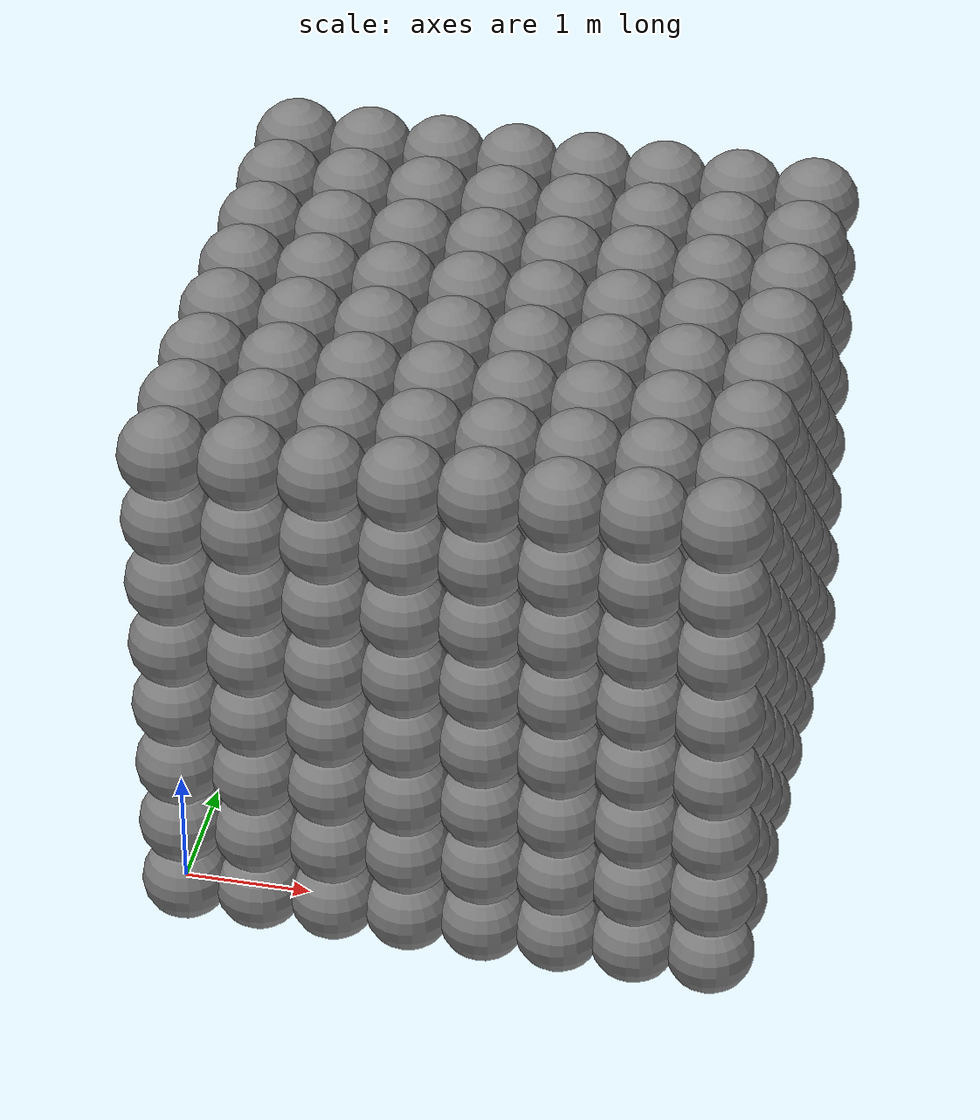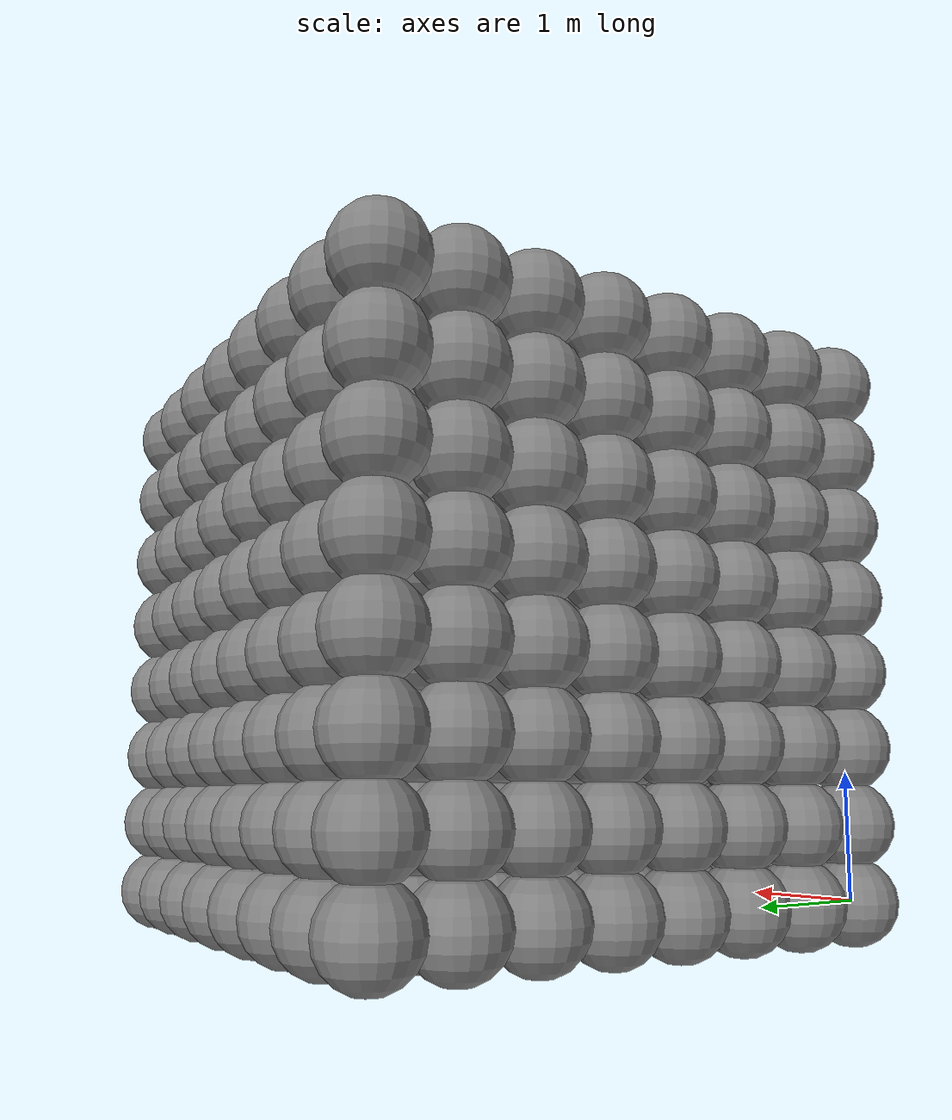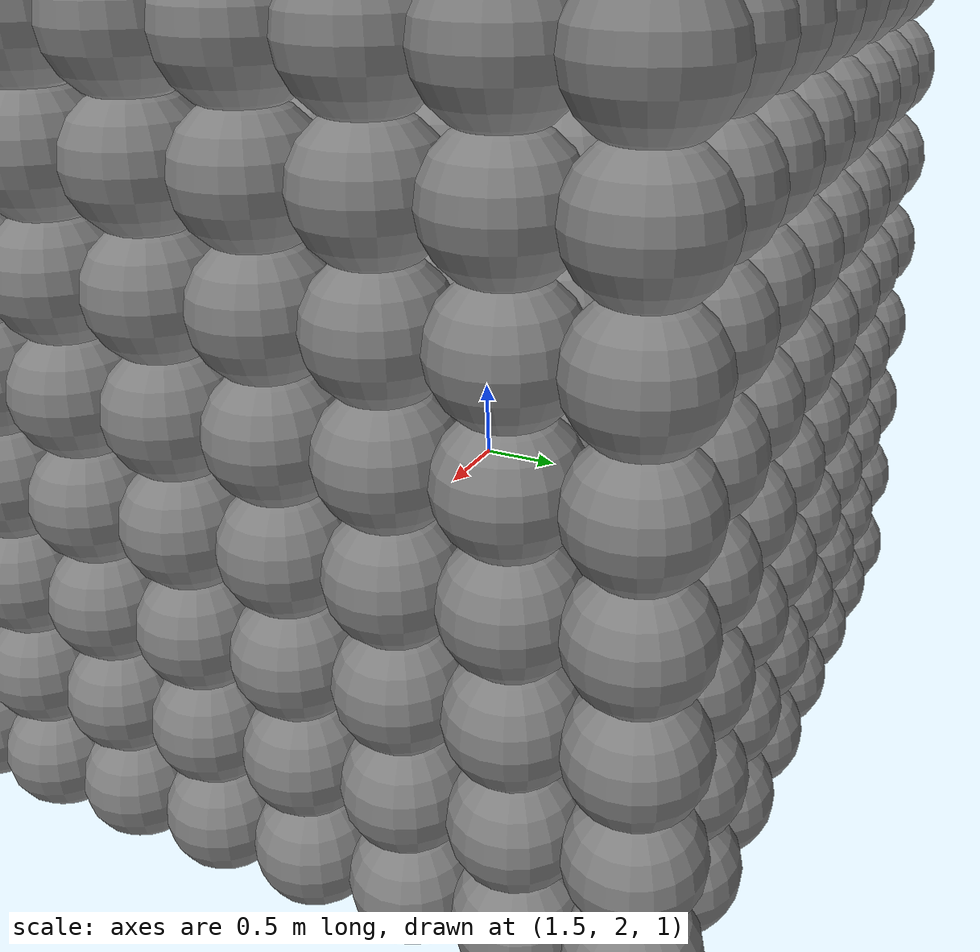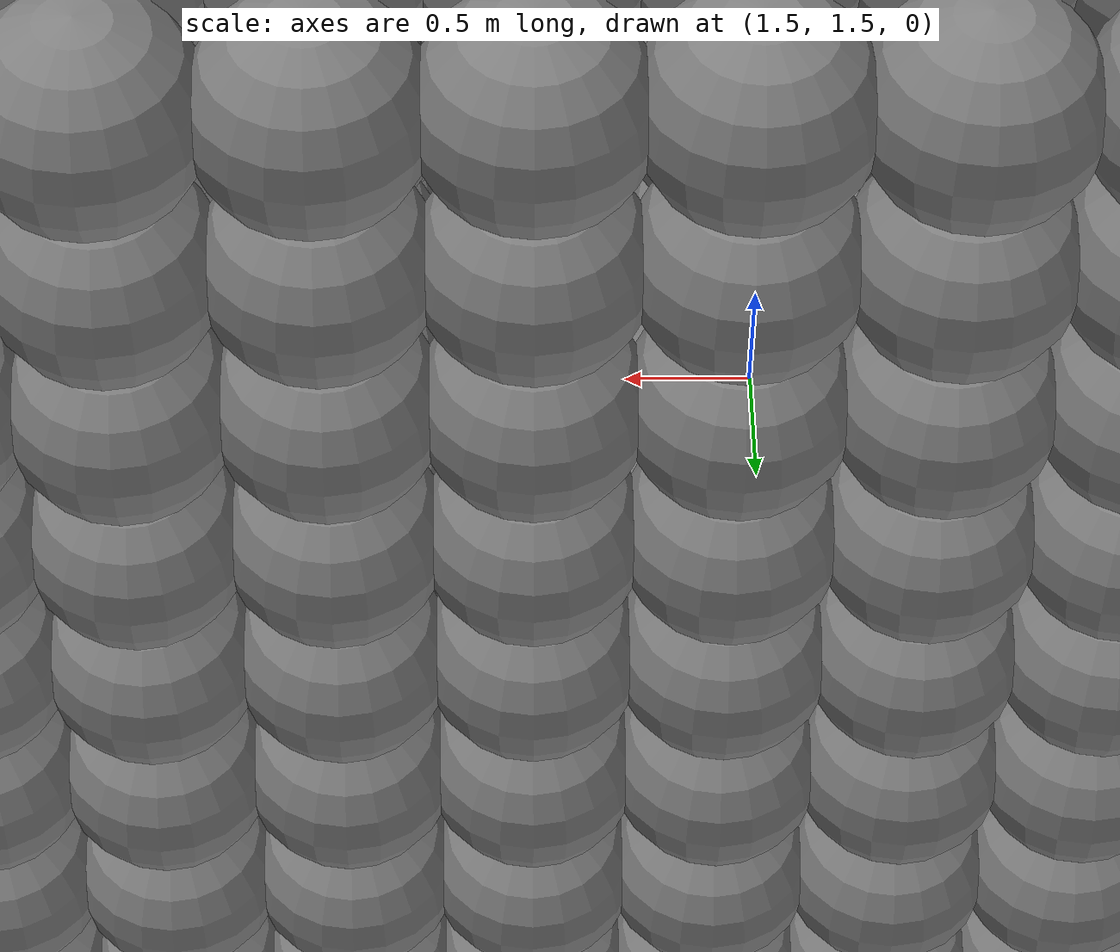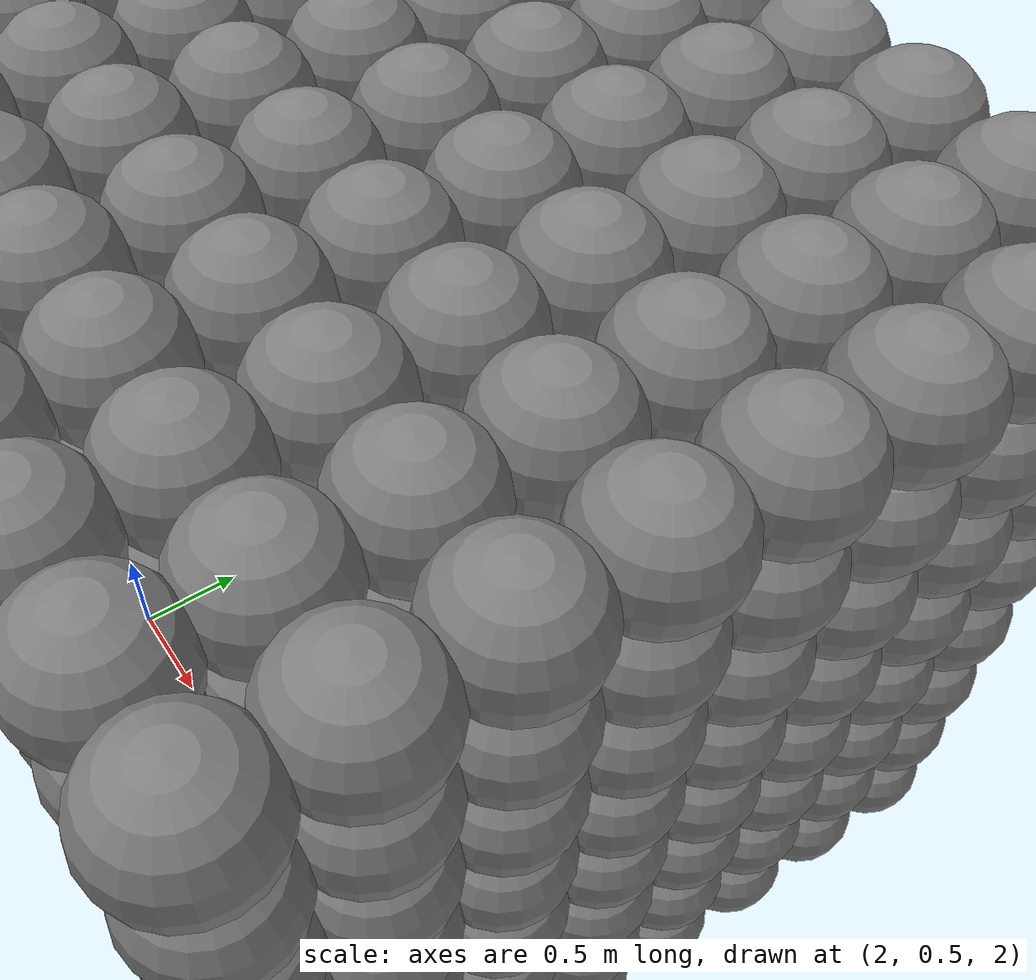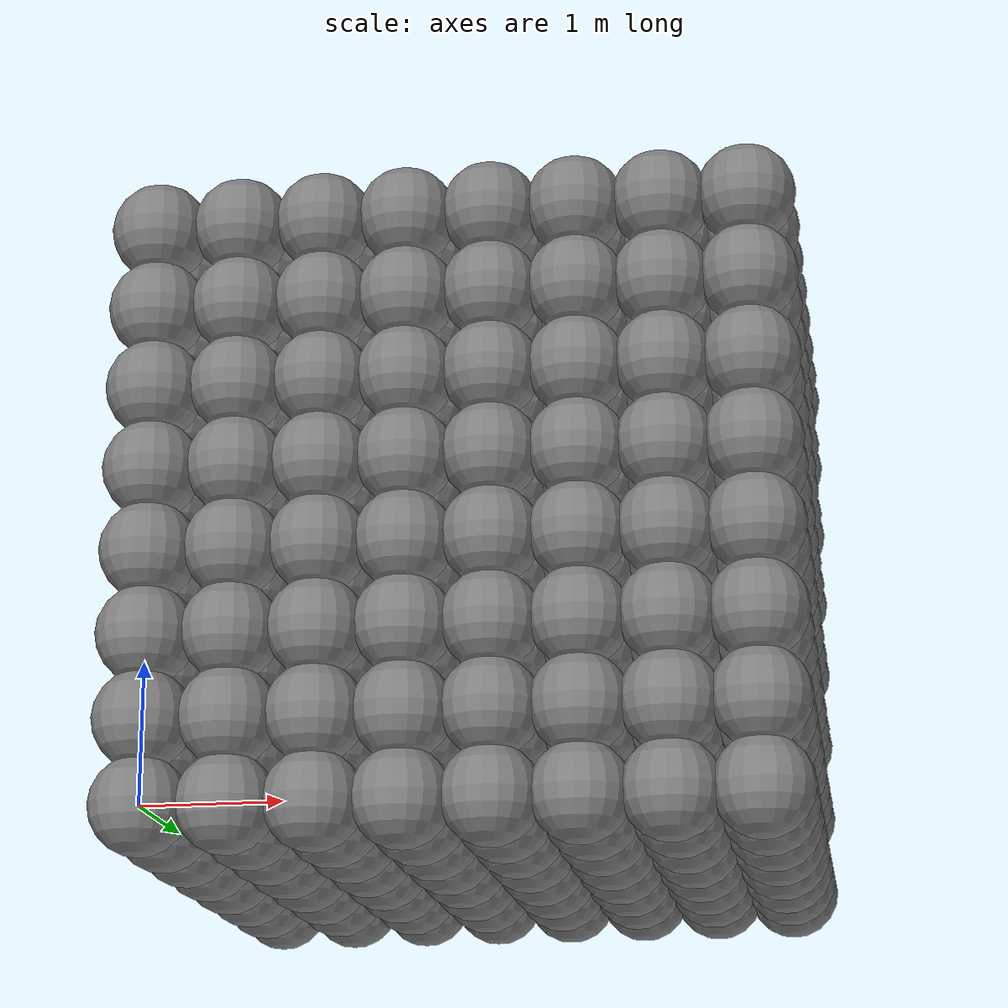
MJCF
<mujoco><option ccd_iterations="100"/><worldbody><body pos="0.0 0.0 0.0"><freejoint/><geom type="sphere" size=".35 .4 .45"/></body><body pos="0.6 0.0 0.0"><freejoint/><geom type="sphere" size=".35 .4 .45"/></body><body pos="1.2 0.0 0.0"><freejoint/><geom type="sphere" size=".35 .4 .45"/></body><body pos="1.7999999999999998 0.0 0.0"><freejoint/><geom type="sphere" size=".35 .4 .45"/></body><body pos="2.4 0.0 0.0"><freejoint/><geom type="sphere" size=".35 .4 .45"/></body><body pos="3.0 0.0 0.0"><freejoint/><geom type="sphere" size=".35 .4 .45"/></body><body pos="3.5999999999999996 0.0 0.0"><freejoint/><geom type="sphere" size=".35 .4 .45"/></body><body pos="4.2 0.0 0.0"><freejoint/><geom type="sphere" size=".35 .4 .45"/></body><body pos="0.0 0.6 0.0"><freejoint/><geom type="sphere" size=".35 .4 .45"/></body><body pos="0.6 0.6 0.0"><freejoint/><geom type="sphere" size=".35 .4 .45"/></body><body pos="1.2 0.6 0.0"><freejoint/><geom type="sphere" size=".35 .4 .45"/></body><body pos="1.7999999999999998 0.6 0.0"><freejoint/><geom type="sphere" size=".35 .4 .45"/></body><body pos="2.4 0.6 0.0"><freejoint/><geom type="sphere" size=".35 .4 .45"/></body><body pos="3.0 0.6 0.0"><freejoint/><geom type="sphere" size=".35 .4 .45"/></body><body pos="3.5999999999999996 0.6 0.0"><freejoint/><geom type="sphere" size=".35 .4 .45"/></body><body pos="4.2 0.6 0.0"><freejoint/><geom type="sphere" size=".35 .4 .45"/></body><body pos="0.0 1.2 0.0"><freejoint/><geom type="sphere" size=".35 .4 .45"/></body><body pos="0.6 1.2 0.0"><freejoint/><geom type="sphere" size=".35 .4 .45"/></body><body pos="1.2 1.2 0.0"><freejoint/><geom type="sphere" size=".35 .4 .45"/></body><body pos="1.7999999999999998 1.2 0.0"><freejoint/><geom type="sphere" size=".35 .4 .45"/></body><body pos="2.4 1.2 0.0"><freejoint/><geom type="sphere" size=".35 .4 .45"/></body><body pos="3.0 1.2 0.0"><freejoint/><geom type="sphere" size=".35 .4 .45"/></body><body pos="3.5999999999999996 1.2 0.0"><freejoint/><geom type="sphere" size=".35 .4 .45"/></body><body pos="4.2 1.2 0.0"><freejoint/><geom type="sphere" size=".35 .4 .45"/></body><body pos="0.0 1.7999999999999998 0.0"><freejoint/><geom type="sphere" size=".35 .4 .45"/></body><body pos="0.6 1.7999999999999998 0.0"><freejoint/><geom type="sphere" size=".35 .4 .45"/></body><body pos="1.2 1.7999999999999998 0.0"><freejoint/><geom type="sphere" size=".35 .4 .45"/></body><body pos="1.7999999999999998 1.7999999999999998 0.0"><freejoint/><geom type="sphere" size=".35 .4 .45"/></body><body pos="2.4 1.7999999999999998 0.0"><freejoint/><geom type="sphere" size=".35 .4 .45"/></body><body pos="3.0 1.7999999999999998 0.0"><freejoint/><geom type="sphere" size=".35 .4 .45"/></body><body pos="3.5999999999999996 1.7999999999999998 0.0"><freejoint/><geom type="sphere" size=".35 .4 .45"/></body><body pos="4.2 1.7999999999999998 0.0"><freejoint/><geom type="sphere" size=".35 .4 .45"/></body><body pos="0.0 2.4 0.0"><freejoint/><geom type="sphere" size=".35 .4 .45"/></body><body pos="0.6 2.4 0.0"><freejoint/><geom type="sphere" size=".35 .4 .45"/></body><body pos="1.2 2.4 0.0"><freejoint/><geom type="sphere" size=".35 .4 .45"/></body><body pos="1.7999999999999998 2.4 0.0"><freejoint/><geom type="sphere" size=".35 .4 .45"/></body><body pos="2.4 2.4 0.0"><freejoint/><geom type="sphere" size=".35 .4 .45"/></body><body pos="3.0 2.4 0.0"><freejoint/><geom type="sphere" size=".35 .4 .45"/></body><body pos="3.5999999999999996 2.4 0.0"><freejoint/><geom type="sphere" size=".35 .4 .45"/></body><body pos="4.2 2.4 0.0"><freejoint/><geom type="sphere" size=".35 .4 .45"/></body><body pos="0.0 3.0 0.0"><freejoint/><geom type="sphere" size=".35 .4 .45"/></body><body pos="0.6 3.0 0.0"><freejoint/><geom type="sphere" size=".35 .4 .45"/></body><body pos="1.2 3.0 0.0"><freejoint/><geom type="sphere" size=".35 .4 .45"/></body><body pos="1.7999999999999998 3.0 0.0"><freejoint/><geom type="sphere" size=".35 .4 .45"/></body><body pos="2.4 3.0 0.0"><freejoint/><geom type="sphere" size=".35 .4 .45"/></body><body pos="3.0 3.0 0.0"><freejoint/><geom type="sphere" size=".35 .4 .45"/></body><body pos="3.5999999999999996 3.0 0.0"><freejoint/><geom type="sphere" size=".35 .4 .45"/></body><body pos="4.2 3.0 0.0"><freejoint/><geom type="sphere" size=".35 .4 .45"/></body><body pos="0.0 3.5999999999999996 0.0"><freejoint/><geom type="sphere" size=".35 .4 .45"/></body><body pos="0.6 3.5999999999999996 0.0"><freejoint/><geom type="sphere" size=".35 .4 .45"/></body><body pos="1.2 3.5999999999999996 0.0"><freejoint/><geom type="sphere" size=".35 .4 .45"/></body><body pos="1.7999999999999998 3.5999999999999996 0.0"><freejoint/><geom type="sphere" size=".35 .4 .45"/></body><body pos="2.4 3.5999999999999996 0.0"><freejoint/><geom type="sphere" size=".35 .4 .45"/></body><body pos="3.0 3.5999999999999996 0.0"><freejoint/><geom type="sphere" size=".35 .4 .45"/></body><body pos="3.5999999999999996 3.5999999999999996 0.0"><freejoint/><geom type="sphere" size=".35 .4 .45"/></body><body pos="4.2 3.5999999999999996 0.0"><freejoint/><geom type="sphere" size=".35 .4 .45"/></body><body pos="0.0 4.2 0.0"><freejoint/><geom type="sphere" size=".35 .4 .45"/></body><body pos="0.6 4.2 0.0"><freejoint/><geom type="sphere" size=".35 .4 .45"/></body><body pos="1.2 4.2 0.0"><freejoint/><geom type="sphere" size=".35 .4 .45"/></body><body pos="1.7999999999999998 4.2 0.0"><freejoint/><geom type="sphere" size=".35 .4 .45"/></body><body pos="2.4 4.2 0.0"><freejoint/><geom type="sphere" size=".35 .4 .45"/></body><body pos="3.0 4.2 0.0"><freejoint/><geom type="sphere" size=".35 .4 .45"/></body><body pos="3.5999999999999996 4.2 0.0"><freejoint/><geom type="sphere" size=".35 .4 .45"/></body><body pos="4.2 4.2 0.0"><freejoint/><geom type="sphere" size=".35 .4 .45"/></body><body pos="0.0 0.0 0.6"><freejoint/><geom type="sphere" size=".35 .4 .45"/></body><body pos="0.6 0.0 0.6"><freejoint/><geom type="sphere" size=".35 .4 .45"/></body><body pos="1.2 0.0 0.6"><freejoint/><geom type="sphere" size=".35 .4 .45"/></body><body pos="1.7999999999999998 0.0 0.6"><freejoint/><geom type="sphere" size=".35 .4 .45"/></body><body pos="2.4 0.0 0.6"><freejoint/><geom type="sphere" size=".35 .4 .45"/></body><body pos="3.0 0.0 0.6"><freejoint/><geom type="sphere" size=".35 .4 .45"/></body><body pos="3.5999999999999996 0.0 0.6"><freejoint/><geom type="sphere" size=".35 .4 .45"/></body><body pos="4.2 0.0 0.6"><freejoint/><geom type="sphere" size=".35 .4 .45"/></body><body pos="0.0 0.6 0.6"><freejoint/><geom type="sphere" size=".35 .4 .45"/></body><body pos="0.6 0.6 0.6"><freejoint/><geom type="sphere" size=".35 .4 .45"/></body><body pos="1.2 0.6 0.6"><freejoint/><geom type="sphere" size=".35 .4 .45"/></body><body pos="1.7999999999999998 0.6 0.6"><freejoint/><geom type="sphere" size=".35 .4 .45"/></body><body pos="2.4 0.6 0.6"><freejoint/><geom type="sphere" size=".35 .4 .45"/></body><body pos="3.0 0.6 0.6"><freejoint/><geom type="sphere" size=".35 .4 .45"/></body><body pos="3.5999999999999996 0.6 0.6"><freejoint/><geom type="sphere" size=".35 .4 .45"/></body><body pos="4.2 0.6 0.6"><freejoint/><geom type="sphere" size=".35 .4 .45"/></body><body pos="0.0 1.2 0.6"><freejoint/><geom type="sphere" size=".35 .4 .45"/></body><body pos="0.6 1.2 0.6"><freejoint/><geom type="sphere" size=".35 .4 .45"/></body><body pos="1.2 1.2 0.6"><freejoint/><geom type="sphere" size=".35 .4 .45"/></body><body pos="1.7999999999999998 1.2 0.6"><freejoint/><geom type="sphere" size=".35 .4 .45"/></body><body pos="2.4 1.2 0.6"><freejoint/><geom type="sphere" size=".35 .4 .45"/></body><body pos="3.0 1.2 0.6"><freejoint/><geom type="sphere" size=".35 .4 .45"/></body><body pos="3.5999999999999996 1.2 0.6"><freejoint/><geom type="sphere" size=".35 .4 .45"/></body><body pos="4.2 1.2 0.6"><freejoint/><geom type="sphere" size=".35 .4 .45"/></body><body pos="0.0 1.7999999999999998 0.6"><freejoint/><geom type="sphere" size=".35 .4 .45"/></body><body pos="0.6 1.7999999999999998 0.6"><freejoint/><geom type="sphere" size=".35 .4 .45"/></body><body pos="1.2 1.7999999999999998 0.6"><freejoint/><geom type="sphere" size=".35 .4 .45"/></body><body pos="1.7999999999999998 1.7999999999999998 0.6"><freejoint/><geom type="sphere" size=".35 .4 .45"/></body><body pos="2.4 1.7999999999999998 0.6"><freejoint/><geom type="sphere" size=".35 .4 .45"/></body><body pos="3.0 1.7999999999999998 0.6"><freejoint/><geom type="sphere" size=".35 .4 .45"/></body><body pos="3.5999999999999996 1.7999999999999998 0.6"><freejoint/><geom type="sphere" size=".35 .4 .45"/></body><body pos="4.2 1.7999999999999998 0.6"><freejoint/><geom type="sphere" size=".35 .4 .45"/></body><body pos="0.0 2.4 0.6"><freejoint/><geom type="sphere" size=".35 .4 .45"/></body><body pos="0.6 2.4 0.6"><freejoint/><geom type="sphere" size=".35 .4 .45"/></body><body pos="1.2 2.4 0.6"><freejoint/><geom type="sphere" size=".35 .4 .45"/></body><body pos="1.7999999999999998 2.4 0.6"><freejoint/><geom type="sphere" size=".35 .4 .45"/></body><body pos="2.4 2.4 0.6"><freejoint/><geom type="sphere" size=".35 .4 .45"/></body><body pos="3.0 2.4 0.6"><freejoint/><geom type="sphere" size=".35 .4 .45"/></body><body pos="3.5999999999999996 2.4 0.6"><freejoint/><geom type="sphere" size=".35 .4 .45"/></body><body pos="4.2 2.4 0.6"><freejoint/><geom type="sphere" size=".35 .4 .45"/></body><body pos="0.0 3.0 0.6"><freejoint/><geom type="sphere" size=".35 .4 .45"/></body><body pos="0.6 3.0 0.6"><freejoint/><geom type="sphere" size=".35 .4 .45"/></body><body pos="1.2 3.0 0.6"><freejoint/><geom type="sphere" size=".35 .4 .45"/></body><body pos="1.7999999999999998 3.0 0.6"><freejoint/><geom type="sphere" size=".35 .4 .45"/></body><body pos="2.4 3.0 0.6"><freejoint/><geom type="sphere" size=".35 .4 .45"/></body><body pos="3.0 3.0 0.6"><freejoint/><geom type="sphere" size=".35 .4 .45"/></body><body pos="3.5999999999999996 3.0 0.6"><freejoint/><geom type="sphere" size=".35 .4 .45"/></body><body pos="4.2 3.0 0.6"><freejoint/><geom type="sphere" size=".35 .4 .45"/></body><body pos="0.0 3.5999999999999996 0.6"><freejoint/><geom type="sphere" size=".35 .4 .45"/></body><body pos="0.6 3.5999999999999996 0.6"><freejoint/><geom type="sphere" size=".35 .4 .45"/></body><body pos="1.2 3.5999999999999996 0.6"><freejoint/><geom type="sphere" size=".35 .4 .45"/></body><body pos="1.7999999999999998 3.5999999999999996 0.6"><freejoint/><geom type="sphere" size=".35 .4 .45"/></body><body pos="2.4 3.5999999999999996 0.6"><freejoint/><geom type="sphere" size=".35 .4 .45"/></body><body pos="3.0 3.5999999999999996 0.6"><freejoint/><geom type="sphere" size=".35 .4 .45"/></body><body pos="3.5999999999999996 3.5999999999999996 0.6"><freejoint/><geom type="sphere" size=".35 .4 .45"/></body><body pos="4.2 3.5999999999999996 0.6"><freejoint/><geom type="sphere" size=".35 .4 .45"/></body><body pos="0.0 4.2 0.6"><freejoint/><geom type="sphere" size=".35 .4 .45"/></body><body pos="0.6 4.2 0.6"><freejoint/><geom type="sphere" size=".35 .4 .45"/></body><body pos="1.2 4.2 0.6"><freejoint/><geom type="sphere" size=".35 .4 .45"/></body><body pos="1.7999999999999998 4.2 0.6"><freejoint/><geom type="sphere" size=".35 .4 .45"/></body><body pos="2.4 4.2 0.6"><freejoint/><geom type="sphere" size=".35 .4 .45"/></body><body pos="3.0 4.2 0.6"><freejoint/><geom type="sphere" size=".35 .4 .45"/></body><body pos="3.5999999999999996 4.2 0.6"><freejoint/><geom type="sphere" size=".35 .4 .45"/></body><body pos="4.2 4.2 0.6"><freejoint/><geom type="sphere" size=".35 .4 .45"/></body><body pos="0.0 0.0 1.2"><freejoint/><geom type="sphere" size=".35 .4 .45"/></body><body pos="0.6 0.0 1.2"><freejoint/><geom type="sphere" size=".35 .4 .45"/></body><body pos="1.2 0.0 1.2"><freejoint/><geom type="sphere" size=".35 .4 .45"/></body><body pos="1.7999999999999998 0.0 1.2"><freejoint/><geom type="sphere" size=".35 .4 .45"/></body><body pos="2.4 0.0 1.2"><freejoint/><geom type="sphere" size=".35 .4 .45"/></body><body pos="3.0 0.0 1.2"><freejoint/><geom type="sphere" size=".35 .4 .45"/></body><body pos="3.5999999999999996 0.0 1.2"><freejoint/><geom type="sphere" size=".35 .4 .45"/></body><body pos="4.2 0.0 1.2"><freejoint/><geom type="sphere" size=".35 .4 .45"/></body><body pos="0.0 0.6 1.2"><freejoint/><geom type="sphere" size=".35 .4 .45"/></body><body pos="0.6 0.6 1.2"><freejoint/><geom type="sphere" size=".35 .4 .45"/></body><body pos="1.2 0.6 1.2"><freejoint/><geom type="sphere" size=".35 .4 .45"/></body><body pos="1.7999999999999998 0.6 1.2"><freejoint/><geom type="sphere" size=".35 .4 .45"/></body><body pos="2.4 0.6 1.2"><freejoint/><geom type="sphere" size=".35 .4 .45"/></body><body pos="3.0 0.6 1.2"><freejoint/><geom type="sphere" size=".35 .4 .45"/></body><body pos="3.5999999999999996 0.6 1.2"><freejoint/><geom type="sphere" size=".35 .4 .45"/></body><body pos="4.2 0.6 1.2"><freejoint/><geom type="sphere" size=".35 .4 .45"/></body><body pos="0.0 1.2 1.2"><freejoint/><geom type="sphere" size=".35 .4 .45"/></body><body pos="0.6 1.2 1.2"><freejoint/><geom type="sphere" size=".35 .4 .45"/></body><body pos="1.2 1.2 1.2"><freejoint/><geom type="sphere" size=".35 .4 .45"/></body><body pos="1.7999999999999998 1.2 1.2"><freejoint/><geom type="sphere" size=".35 .4 .45"/></body><body pos="2.4 1.2 1.2"><freejoint/><geom type="sphere" size=".35 .4 .45"/></body><body pos="3.0 1.2 1.2"><freejoint/><geom type="sphere" size=".35 .4 .45"/></body><body pos="3.5999999999999996 1.2 1.2"><freejoint/><geom type="sphere" size=".35 .4 .45"/></body><body pos="4.2 1.2 1.2"><freejoint/><geom type="sphere" size=".35 .4 .45"/></body><body pos="0.0 1.7999999999999998 1.2"><freejoint/><geom type="sphere" size=".35 .4 .45"/></body><body pos="0.6 1.7999999999999998 1.2"><freejoint/><geom type="sphere" size=".35 .4 .45"/></body><body pos="1.2 1.7999999999999998 1.2"><freejoint/><geom type="sphere" size=".35 .4 .45"/></body><body pos="1.7999999999999998 1.7999999999999998 1.2"><freejoint/><geom type="sphere" size=".35 .4 .45"/></body><body pos="2.4 1.7999999999999998 1.2"><freejoint/><geom type="sphere" size=".35 .4 .45"/></body><body pos="3.0 1.7999999999999998 1.2"><freejoint/><geom type="sphere" size=".35 .4 .45"/></body><body pos="3.5999999999999996 1.7999999999999998 1.2"><freejoint/><geom type="sphere" size=".35 .4 .45"/></body><body pos="4.2 1.7999999999999998 1.2"><freejoint/><geom type="sphere" size=".35 .4 .45"/></body><body pos="0.0 2.4 1.2"><freejoint/><geom type="sphere" size=".35 .4 .45"/></body><body pos="0.6 2.4 1.2"><freejoint/><geom type="sphere" size=".35 .4 .45"/></body><body pos="1.2 2.4 1.2"><freejoint/><geom type="sphere" size=".35 .4 .45"/></body><body pos="1.7999999999999998 2.4 1.2"><freejoint/><geom type="sphere" size=".35 .4 .45"/></body><body pos="2.4 2.4 1.2"><freejoint/><geom type="sphere" size=".35 .4 .45"/></body><body pos="3.0 2.4 1.2"><freejoint/><geom type="sphere" size=".35 .4 .45"/></body><body pos="3.5999999999999996 2.4 1.2"><freejoint/><geom type="sphere" size=".35 .4 .45"/></body><body pos="4.2 2.4 1.2"><freejoint/><geom type="sphere" size=".35 .4 .45"/></body><body pos="0.0 3.0 1.2"><freejoint/><geom type="sphere" size=".35 .4 .45"/></body><body pos="0.6 3.0 1.2"><freejoint/><geom type="sphere" size=".35 .4 .45"/></body><body pos="1.2 3.0 1.2"><freejoint/><geom type="sphere" size=".35 .4 .45"/></body><body pos="1.7999999999999998 3.0 1.2"><freejoint/><geom type="sphere" size=".35 .4 .45"/></body><body pos="2.4 3.0 1.2"><freejoint/><geom type="sphere" size=".35 .4 .45"/></body><body pos="3.0 3.0 1.2"><freejoint/><geom type="sphere" size=".35 .4 .45"/></body><body pos="3.5999999999999996 3.0 1.2"><freejoint/><geom type="sphere" size=".35 .4 .45"/></body><body pos="4.2 3.0 1.2"><freejoint/><geom type="sphere" size=".35 .4 .45"/></body><body pos="0.0 3.5999999999999996 1.2"><freejoint/><geom type="sphere" size=".35 .4 .45"/></body><body pos="0.6 3.5999999999999996 1.2"><freejoint/><geom type="sphere" size=".35 .4 .45"/></body><body pos="1.2 3.5999999999999996 1.2"><freejoint/><geom type="sphere" size=".35 .4 .45"/></body><body pos="1.7999999999999998 3.5999999999999996 1.2"><freejoint/><geom type="sphere" size=".35 .4 .45"/></body><body pos="2.4 3.5999999999999996 1.2"><freejoint/><geom type="sphere" size=".35 .4 .45"/></body><body pos="3.0 3.5999999999999996 1.2"><freejoint/><geom type="sphere" size=".35 .4 .45"/></body><body pos="3.5999999999999996 3.5999999999999996 1.2"><freejoint/><geom type="sphere" size=".35 .4 .45"/></body><body pos="4.2 3.5999999999999996 1.2"><freejoint/><geom type="sphere" size=".35 .4 .45"/></body><body pos="0.0 4.2 1.2"><freejoint/><geom type="sphere" size=".35 .4 .45"/></body><body pos="0.6 4.2 1.2"><freejoint/><geom type="sphere" size=".35 .4 .45"/></body><body pos="1.2 4.2 1.2"><freejoint/><geom type="sphere" size=".35 .4 .45"/></body><body pos="1.7999999999999998 4.2 1.2"><freejoint/><geom type="sphere" size=".35 .4 .45"/></body><body pos="2.4 4.2 1.2"><freejoint/><geom type="sphere" size=".35 .4 .45"/></body><body pos="3.0 4.2 1.2"><freejoint/><geom type="sphere" size=".35 .4 .45"/></body><body pos="3.5999999999999996 4.2 1.2"><freejoint/><geom type="sphere" size=".35 .4 .45"/></body><body pos="4.2 4.2 1.2"><freejoint/><geom type="sphere" size=".35 .4 .45"/></body><body pos="0.0 0.0 1.7999999999999998"><freejoint/><geom type="sphere" size=".35 .4 .45"/></body><body pos="0.6 0.0 1.7999999999999998"><freejoint/><geom type="sphere" size=".35 .4 .45"/></body><body pos="1.2 0.0 1.7999999999999998"><freejoint/><geom type="sphere" size=".35 .4 .45"/></body><body pos="1.7999999999999998 0.0 1.7999999999999998"><freejoint/><geom type="sphere" size=".35 .4 .45"/></body><body pos="2.4 0.0 1.7999999999999998"><freejoint/><geom type="sphere" size=".35 .4 .45"/></body><body pos="3.0 0.0 1.7999999999999998"><freejoint/><geom type="sphere" size=".35 .4 .45"/></body><body pos="3.5999999999999996 0.0 1.7999999999999998"><freejoint/><geom type="sphere" size=".35 .4 .45"/></body><body pos="4.2 0.0 1.7999999999999998"><freejoint/><geom type="sphere" size=".35 .4 .45"/></body><body pos="0.0 0.6 1.7999999999999998"><freejoint/><geom type="sphere" size=".35 .4 .45"/></body><body pos="0.6 0.6 1.7999999999999998"><freejoint/><geom type="sphere" size=".35 .4 .45"/></body><body pos="1.2 0.6 1.7999999999999998"><freejoint/><geom type="sphere" size=".35 .4 .45"/></body><body pos="1.7999999999999998 0.6 1.7999999999999998"><freejoint/><geom type="sphere" size=".35 .4 .45"/></body><body pos="2.4 0.6 1.7999999999999998"><freejoint/><geom type="sphere" size=".35 .4 .45"/></body><body pos="3.0 0.6 1.7999999999999998"><freejoint/><geom type="sphere" size=".35 .4 .45"/></body><body pos="3.5999999999999996 0.6 1.7999999999999998"><freejoint/><geom type="sphere" size=".35 .4 .45"/></body><body pos="4.2 0.6 1.7999999999999998"><freejoint/><geom type="sphere" size=".35 .4 .45"/></body><body pos="0.0 1.2 1.7999999999999998"><freejoint/><geom type="sphere" size=".35 .4 .45"/></body><body pos="0.6 1.2 1.7999999999999998"><freejoint/><geom type="sphere" size=".35 .4 .45"/></body><body pos="1.2 1.2 1.7999999999999998"><freejoint/><geom type="sphere" size=".35 .4 .45"/></body><body pos="1.7999999999999998 1.2 1.7999999999999998"><freejoint/><geom type="sphere" size=".35 .4 .45"/></body><body pos="2.4 1.2 1.7999999999999998"><freejoint/><geom type="sphere" size=".35 .4 .45"/></body><body pos="3.0 1.2 1.7999999999999998"><freejoint/><geom type="sphere" size=".35 .4 .45"/></body><body pos="3.5999999999999996 1.2 1.7999999999999998"><freejoint/><geom type="sphere" size=".35 .4 .45"/></body><body pos="4.2 1.2 1.7999999999999998"><freejoint/><geom type="sphere" size=".35 .4 .45"/></body><body pos="0.0 1.7999999999999998 1.7999999999999998"><freejoint/><geom type="sphere" size=".35 .4 .45"/></body><body pos="0.6 1.7999999999999998 1.7999999999999998"><freejoint/><geom type="sphere" size=".35 .4 .45"/></body><body pos="1.2 1.7999999999999998 1.7999999999999998"><freejoint/><geom type="sphere" size=".35 .4 .45"/></body><body pos="1.7999999999999998 1.7999999999999998 1.7999999999999998"><freejoint/><geom type="sphere" size=".35 .4 .45"/></body><body pos="2.4 1.7999999999999998 1.7999999999999998"><freejoint/><geom type="sphere" size=".35 .4 .45"/></body><body pos="3.0 1.7999999999999998 1.7999999999999998"><freejoint/><geom type="sphere" size=".35 .4 .45"/></body><body pos="3.5999999999999996 1.7999999999999998 1.7999999999999998"><freejoint/><geom type="sphere" size=".35 .4 .45"/></body><body pos="4.2 1.7999999999999998 1.7999999999999998"><freejoint/><geom type="sphere" size=".35 .4 .45"/></body><body pos="0.0 2.4 1.7999999999999998"><freejoint/><geom type="sphere" size=".35 .4 .45"/></body><body pos="0.6 2.4 1.7999999999999998"><freejoint/><geom type="sphere" size=".35 .4 .45"/></body><body pos="1.2 2.4 1.7999999999999998"><freejoint/><geom type="sphere" size=".35 .4 .45"/></body><body pos="1.7999999999999998 2.4 1.7999999999999998"><freejoint/><geom type="sphere" size=".35 .4 .45"/></body><body pos="2.4 2.4 1.7999999999999998"><freejoint/><geom type="sphere" size=".35 .4 .45"/></body><body pos="3.0 2.4 1.7999999999999998"><freejoint/><geom type="sphere" size=".35 .4 .45"/></body><body pos="3.5999999999999996 2.4 1.7999999999999998"><freejoint/><geom type="sphere" size=".35 .4 .45"/></body><body pos="4.2 2.4 1.7999999999999998"><freejoint/><geom type="sphere" size=".35 .4 .45"/></body><body pos="0.0 3.0 1.7999999999999998"><freejoint/><geom type="sphere" size=".35 .4 .45"/></body><body pos="0.6 3.0 1.7999999999999998"><freejoint/><geom type="sphere" size=".35 .4 .45"/></body><body pos="1.2 3.0 1.7999999999999998"><freejoint/><geom type="sphere" size=".35 .4 .45"/></body><body pos="1.7999999999999998 3.0 1.7999999999999998"><freejoint/><geom type="sphere" size=".35 .4 .45"/></body><body pos="2.4 3.0 1.7999999999999998"><freejoint/><geom type="sphere" size=".35 .4 .45"/></body><body pos="3.0 3.0 1.7999999999999998"><freejoint/><geom type="sphere" size=".35 .4 .45"/></body><body pos="3.5999999999999996 3.0 1.7999999999999998"><freejoint/><geom type="sphere" size=".35 .4 .45"/></body><body pos="4.2 3.0 1.7999999999999998"><freejoint/><geom type="sphere" size=".35 .4 .45"/></body><body pos="0.0 3.5999999999999996 1.7999999999999998"><freejoint/><geom type="sphere" size=".35 .4 .45"/></body><body pos="0.6 3.5999999999999996 1.7999999999999998"><freejoint/><geom type="sphere" size=".35 .4 .45"/></body><body pos="1.2 3.5999999999999996 1.7999999999999998"><freejoint/><geom type="sphere" size=".35 .4 .45"/></body><body pos="1.7999999999999998 3.5999999999999996 1.7999999999999998"><freejoint/><geom type="sphere" size=".35 .4 .45"/></body><body pos="2.4 3.5999999999999996 1.7999999999999998"><freejoint/><geom type="sphere" size=".35 .4 .45"/></body><body pos="3.0 3.5999999999999996 1.7999999999999998"><freejoint/><geom type="sphere" size=".35 .4 .45"/></body><body pos="3.5999999999999996 3.5999999999999996 1.7999999999999998"><freejoint/><geom type="sphere" size=".35 .4 .45"/></body><body pos="4.2 3.5999999999999996 1.7999999999999998"><freejoint/><geom type="sphere" size=".35 .4 .45"/></body><body pos="0.0 4.2 1.7999999999999998"><freejoint/><geom type="sphere" size=".35 .4 .45"/></body><body pos="0.6 4.2 1.7999999999999998"><freejoint/><geom type="sphere" size=".35 .4 .45"/></body><body pos="1.2 4.2 1.7999999999999998"><freejoint/><geom type="sphere" size=".35 .4 .45"/></body><body pos="1.7999999999999998 4.2 1.7999999999999998"><freejoint/><geom type="sphere" size=".35 .4 .45"/></body><body pos="2.4 4.2 1.7999999999999998"><freejoint/><geom type="sphere" size=".35 .4 .45"/></body><body pos="3.0 4.2 1.7999999999999998"><freejoint/><geom type="sphere" size=".35 .4 .45"/></body><body pos="3.5999999999999996 4.2 1.7999999999999998"><freejoint/><geom type="sphere" size=".35 .4 .45"/></body><body pos="4.2 4.2 1.7999999999999998"><freejoint/><geom type="sphere" size=".35 .4 .45"/></body><body pos="0.0 0.0 2.4"><freejoint/><geom type="sphere" size=".35 .4 .45"/></body><body pos="0.6 0.0 2.4"><freejoint/><geom type="sphere" size=".35 .4 .45"/></body><body pos="1.2 0.0 2.4"><freejoint/><geom type="sphere" size=".35 .4 .45"/></body><body pos="1.7999999999999998 0.0 2.4"><freejoint/><geom type="sphere" size=".35 .4 .45"/></body><body pos="2.4 0.0 2.4"><freejoint/><geom type="sphere" size=".35 .4 .45"/></body><body pos="3.0 0.0 2.4"><freejoint/><geom type="sphere" size=".35 .4 .45"/></body><body pos="3.5999999999999996 0.0 2.4"><freejoint/><geom type="sphere" size=".35 .4 .45"/></body><body pos="4.2 0.0 2.4"><freejoint/><geom type="sphere" size=".35 .4 .45"/></body><body pos="0.0 0.6 2.4"><freejoint/><geom type="sphere" size=".35 .4 .45"/></body><body pos="0.6 0.6 2.4"><freejoint/><geom type="sphere" size=".35 .4 .45"/></body><body pos="1.2 0.6 2.4"><freejoint/><geom type="sphere" size=".35 .4 .45"/></body><body pos="1.7999999999999998 0.6 2.4"><freejoint/><geom type="sphere" size=".35 .4 .45"/></body><body pos="2.4 0.6 2.4"><freejoint/><geom type="sphere" size=".35 .4 .45"/></body><body pos="3.0 0.6 2.4"><freejoint/><geom type="sphere" size=".35 .4 .45"/></body><body pos="3.5999999999999996 0.6 2.4"><freejoint/><geom type="sphere" size=".35 .4 .45"/></body><body pos="4.2 0.6 2.4"><freejoint/><geom type="sphere" size=".35 .4 .45"/></body><body pos="0.0 1.2 2.4"><freejoint/><geom type="sphere" size=".35 .4 .45"/></body><body pos="0.6 1.2 2.4"><freejoint/><geom type="sphere" size=".35 .4 .45"/></body><body pos="1.2 1.2 2.4"><freejoint/><geom type="sphere" size=".35 .4 .45"/></body><body pos="1.7999999999999998 1.2 2.4"><freejoint/><geom type="sphere" size=".35 .4 .45"/></body><body pos="2.4 1.2 2.4"><freejoint/><geom type="sphere" size=".35 .4 .45"/></body><body pos="3.0 1.2 2.4"><freejoint/><geom type="sphere" size=".35 .4 .45"/></body><body pos="3.5999999999999996 1.2 2.4"><freejoint/><geom type="sphere" size=".35 .4 .45"/></body><body pos="4.2 1.2 2.4"><freejoint/><geom type="sphere" size=".35 .4 .45"/></body><body pos="0.0 1.7999999999999998 2.4"><freejoint/><geom type="sphere" size=".35 .4 .45"/></body><body pos="0.6 1.7999999999999998 2.4"><freejoint/><geom type="sphere" size=".35 .4 .45"/></body><body pos="1.2 1.7999999999999998 2.4"><freejoint/><geom type="sphere" size=".35 .4 .45"/></body><body pos="1.7999999999999998 1.7999999999999998 2.4"><freejoint/><geom type="sphere" size=".35 .4 .45"/></body><body pos="2.4 1.7999999999999998 2.4"><freejoint/><geom type="sphere" size=".35 .4 .45"/></body><body pos="3.0 1.7999999999999998 2.4"><freejoint/><geom type="sphere" size=".35 .4 .45"/></body><body pos="3.5999999999999996 1.7999999999999998 2.4"><freejoint/><geom type="sphere" size=".35 .4 .45"/></body><body pos="4.2 1.7999999999999998 2.4"><freejoint/><geom type="sphere" size=".35 .4 .45"/></body><body pos="0.0 2.4 2.4"><freejoint/><geom type="sphere" size=".35 .4 .45"/></body><body pos="0.6 2.4 2.4"><freejoint/><geom type="sphere" size=".35 .4 .45"/></body><body pos="1.2 2.4 2.4"><freejoint/><geom type="sphere" size=".35 .4 .45"/></body><body pos="1.7999999999999998 2.4 2.4"><freejoint/><geom type="sphere" size=".35 .4 .45"/></body><body pos="2.4 2.4 2.4"><freejoint/><geom type="sphere" size=".35 .4 .45"/></body><body pos="3.0 2.4 2.4"><freejoint/><geom type="sphere" size=".35 .4 .45"/></body><body pos="3.5999999999999996 2.4 2.4"><freejoint/><geom type="sphere" size=".35 .4 .45"/></body><body pos="4.2 2.4 2.4"><freejoint/><geom type="sphere" size=".35 .4 .45"/></body><body pos="0.0 3.0 2.4"><freejoint/><geom type="sphere" size=".35 .4 .45"/></body><body pos="0.6 3.0 2.4"><freejoint/><geom type="sphere" size=".35 .4 .45"/></body><body pos="1.2 3.0 2.4"><freejoint/><geom type="sphere" size=".35 .4 .45"/></body><body pos="1.7999999999999998 3.0 2.4"><freejoint/><geom type="sphere" size=".35 .4 .45"/></body><body pos="2.4 3.0 2.4"><freejoint/><geom type="sphere" size=".35 .4 .45"/></body><body pos="3.0 3.0 2.4"><freejoint/><geom type="sphere" size=".35 .4 .45"/></body><body pos="3.5999999999999996 3.0 2.4"><freejoint/><geom type="sphere" size=".35 .4 .45"/></body><body pos="4.2 3.0 2.4"><freejoint/><geom type="sphere" size=".35 .4 .45"/></body><body pos="0.0 3.5999999999999996 2.4"><freejoint/><geom type="sphere" size=".35 .4 .45"/></body><body pos="0.6 3.5999999999999996 2.4"><freejoint/><geom type="sphere" size=".35 .4 .45"/></body><body pos="1.2 3.5999999999999996 2.4"><freejoint/><geom type="sphere" size=".35 .4 .45"/></body><body pos="1.7999999999999998 3.5999999999999996 2.4"><freejoint/><geom type="sphere" size=".35 .4 .45"/></body><body pos="2.4 3.5999999999999996 2.4"><freejoint/><geom type="sphere" size=".35 .4 .45"/></body><body pos="3.0 3.5999999999999996 2.4"><freejoint/><geom type="sphere" size=".35 .4 .45"/></body><body pos="3.5999999999999996 3.5999999999999996 2.4"><freejoint/><geom type="sphere" size=".35 .4 .45"/></body><body pos="4.2 3.5999999999999996 2.4"><freejoint/><geom type="sphere" size=".35 .4 .45"/></body><body pos="0.0 4.2 2.4"><freejoint/><geom type="sphere" size=".35 .4 .45"/></body><body pos="0.6 4.2 2.4"><freejoint/><geom type="sphere" size=".35 .4 .45"/></body><body pos="1.2 4.2 2.4"><freejoint/><geom type="sphere" size=".35 .4 .45"/></body><body pos="1.7999999999999998 4.2 2.4"><freejoint/><geom type="sphere" size=".35 .4 .45"/></body><body pos="2.4 4.2 2.4"><freejoint/><geom type="sphere" size=".35 .4 .45"/></body><body pos="3.0 4.2 2.4"><freejoint/><geom type="sphere" size=".35 .4 .45"/></body><body pos="3.5999999999999996 4.2 2.4"><freejoint/><geom type="sphere" size=".35 .4 .45"/></body><body pos="4.2 4.2 2.4"><freejoint/><geom type="sphere" size=".35 .4 .45"/></body><body pos="0.0 0.0 3.0"><freejoint/><geom type="sphere" size=".35 .4 .45"/></body><body pos="0.6 0.0 3.0"><freejoint/><geom type="sphere" size=".35 .4 .45"/></body><body pos="1.2 0.0 3.0"><freejoint/><geom type="sphere" size=".35 .4 .45"/></body><body pos="1.7999999999999998 0.0 3.0"><freejoint/><geom type="sphere" size=".35 .4 .45"/></body><body pos="2.4 0.0 3.0"><freejoint/><geom type="sphere" size=".35 .4 .45"/></body><body pos="3.0 0.0 3.0"><freejoint/><geom type="sphere" size=".35 .4 .45"/></body><body pos="3.5999999999999996 0.0 3.0"><freejoint/><geom type="sphere" size=".35 .4 .45"/></body><body pos="4.2 0.0 3.0"><freejoint/><geom type="sphere" size=".35 .4 .45"/></body><body pos="0.0 0.6 3.0"><freejoint/><geom type="sphere" size=".35 .4 .45"/></body><body pos="0.6 0.6 3.0"><freejoint/><geom type="sphere" size=".35 .4 .45"/></body><body pos="1.2 0.6 3.0"><freejoint/><geom type="sphere" size=".35 .4 .45"/></body><body pos="1.7999999999999998 0.6 3.0"><freejoint/><geom type="sphere" size=".35 .4 .45"/></body><body pos="2.4 0.6 3.0"><freejoint/><geom type="sphere" size=".35 .4 .45"/></body><body pos="3.0 0.6 3.0"><freejoint/><geom type="sphere" size=".35 .4 .45"/></body><body pos="3.5999999999999996 0.6 3.0"><freejoint/><geom type="sphere" size=".35 .4 .45"/></body><body pos="4.2 0.6 3.0"><freejoint/><geom type="sphere" size=".35 .4 .45"/></body><body pos="0.0 1.2 3.0"><freejoint/><geom type="sphere" size=".35 .4 .45"/></body><body pos="0.6 1.2 3.0"><freejoint/><geom type="sphere" size=".35 .4 .45"/></body><body pos="1.2 1.2 3.0"><freejoint/><geom type="sphere" size=".35 .4 .45"/></body><body pos="1.7999999999999998 1.2 3.0"><freejoint/><geom type="sphere" size=".35 .4 .45"/></body><body pos="2.4 1.2 3.0"><freejoint/><geom type="sphere" size=".35 .4 .45"/></body><body pos="3.0 1.2 3.0"><freejoint/><geom type="sphere" size=".35 .4 .45"/></body><body pos="3.5999999999999996 1.2 3.0"><freejoint/><geom type="sphere" size=".35 .4 .45"/></body><body pos="4.2 1.2 3.0"><freejoint/><geom type="sphere" size=".35 .4 .45"/></body><body pos="0.0 1.7999999999999998 3.0"><freejoint/><geom type="sphere" size=".35 .4 .45"/></body><body pos="0.6 1.7999999999999998 3.0"><freejoint/><geom type="sphere" size=".35 .4 .45"/></body><body pos="1.2 1.7999999999999998 3.0"><freejoint/><geom type="sphere" size=".35 .4 .45"/></body><body pos="1.7999999999999998 1.7999999999999998 3.0"><freejoint/><geom type="sphere" size=".35 .4 .45"/></body><body pos="2.4 1.7999999999999998 3.0"><freejoint/><geom type="sphere" size=".35 .4 .45"/></body><body pos="3.0 1.7999999999999998 3.0"><freejoint/><geom type="sphere" size=".35 .4 .45"/></body><body pos="3.5999999999999996 1.7999999999999998 3.0"><freejoint/><geom type="sphere" size=".35 .4 .45"/></body><body pos="4.2 1.7999999999999998 3.0"><freejoint/><geom type="sphere" size=".35 .4 .45"/></body><body pos="0.0 2.4 3.0"><freejoint/><geom type="sphere" size=".35 .4 .45"/></body><body pos="0.6 2.4 3.0"><freejoint/><geom type="sphere" size=".35 .4 .45"/></body><body pos="1.2 2.4 3.0"><freejoint/><geom type="sphere" size=".35 .4 .45"/></body><body pos="1.7999999999999998 2.4 3.0"><freejoint/><geom type="sphere" size=".35 .4 .45"/></body><body pos="2.4 2.4 3.0"><freejoint/><geom type="sphere" size=".35 .4 .45"/></body><body pos="3.0 2.4 3.0"><freejoint/><geom type="sphere" size=".35 .4 .45"/></body><body pos="3.5999999999999996 2.4 3.0"><freejoint/><geom type="sphere" size=".35 .4 .45"/></body><body pos="4.2 2.4 3.0"><freejoint/><geom type="sphere" size=".35 .4 .45"/></body><body pos="0.0 3.0 3.0"><freejoint/><geom type="sphere" size=".35 .4 .45"/></body><body pos="0.6 3.0 3.0"><freejoint/><geom type="sphere" size=".35 .4 .45"/></body><body pos="1.2 3.0 3.0"><freejoint/><geom type="sphere" size=".35 .4 .45"/></body><body pos="1.7999999999999998 3.0 3.0"><freejoint/><geom type="sphere" size=".35 .4 .45"/></body><body pos="2.4 3.0 3.0"><freejoint/><geom type="sphere" size=".35 .4 .45"/></body><body pos="3.0 3.0 3.0"><freejoint/><geom type="sphere" size=".35 .4 .45"/></body><body pos="3.5999999999999996 3.0 3.0"><freejoint/><geom type="sphere" size=".35 .4 .45"/></body><body pos="4.2 3.0 3.0"><freejoint/><geom type="sphere" size=".35 .4 .45"/></body><body pos="0.0 3.5999999999999996 3.0"><freejoint/><geom type="sphere" size=".35 .4 .45"/></body><body pos="0.6 3.5999999999999996 3.0"><freejoint/><geom type="sphere" size=".35 .4 .45"/></body><body pos="1.2 3.5999999999999996 3.0"><freejoint/><geom type="sphere" size=".35 .4 .45"/></body><body pos="1.7999999999999998 3.5999999999999996 3.0"><freejoint/><geom type="sphere" size=".35 .4 .45"/></body><body pos="2.4 3.5999999999999996 3.0"><freejoint/><geom type="sphere" size=".35 .4 .45"/></body><body pos="3.0 3.5999999999999996 3.0"><freejoint/><geom type="sphere" size=".35 .4 .45"/></body><body pos="3.5999999999999996 3.5999999999999996 3.0"><freejoint/><geom type="sphere" size=".35 .4 .45"/></body><body pos="4.2 3.5999999999999996 3.0"><freejoint/><geom type="sphere" size=".35 .4 .45"/></body><body pos="0.0 4.2 3.0"><freejoint/><geom type="sphere" size=".35 .4 .45"/></body><body pos="0.6 4.2 3.0"><freejoint/><geom type="sphere" size=".35 .4 .45"/></body><body pos="1.2 4.2 3.0"><freejoint/><geom type="sphere" size=".35 .4 .45"/></body><body pos="1.7999999999999998 4.2 3.0"><freejoint/><geom type="sphere" size=".35 .4 .45"/></body><body pos="2.4 4.2 3.0"><freejoint/><geom type="sphere" size=".35 .4 .45"/></body><body pos="3.0 4.2 3.0"><freejoint/><geom type="sphere" size=".35 .4 .45"/></body><body pos="3.5999999999999996 4.2 3.0"><freejoint/><geom type="sphere" size=".35 .4 .45"/></body><body pos="4.2 4.2 3.0"><freejoint/><geom type="sphere" size=".35 .4 .45"/></body><body pos="0.0 0.0 3.5999999999999996"><freejoint/><geom type="sphere" size=".35 .4 .45"/></body><body pos="0.6 0.0 3.5999999999999996"><freejoint/><geom type="sphere" size=".35 .4 .45"/></body><body pos="1.2 0.0 3.5999999999999996"><freejoint/><geom type="sphere" size=".35 .4 .45"/></body><body pos="1.7999999999999998 0.0 3.5999999999999996"><freejoint/><geom type="sphere" size=".35 .4 .45"/></body><body pos="2.4 0.0 3.5999999999999996"><freejoint/><geom type="sphere" size=".35 .4 .45"/></body><body pos="3.0 0.0 3.5999999999999996"><freejoint/><geom type="sphere" size=".35 .4 .45"/></body><body pos="3.5999999999999996 0.0 3.5999999999999996"><freejoint/><geom type="sphere" size=".35 .4 .45"/></body><body pos="4.2 0.0 3.5999999999999996"><freejoint/><geom type="sphere" size=".35 .4 .45"/></body><body pos="0.0 0.6 3.5999999999999996"><freejoint/><geom type="sphere" size=".35 .4 .45"/></body><body pos="0.6 0.6 3.5999999999999996"><freejoint/><geom type="sphere" size=".35 .4 .45"/></body><body pos="1.2 0.6 3.5999999999999996"><freejoint/><geom type="sphere" size=".35 .4 .45"/></body><body pos="1.7999999999999998 0.6 3.5999999999999996"><freejoint/><geom type="sphere" size=".35 .4 .45"/></body><body pos="2.4 0.6 3.5999999999999996"><freejoint/><geom type="sphere" size=".35 .4 .45"/></body><body pos="3.0 0.6 3.5999999999999996"><freejoint/><geom type="sphere" size=".35 .4 .45"/></body><body pos="3.5999999999999996 0.6 3.5999999999999996"><freejoint/><geom type="sphere" size=".35 .4 .45"/></body><body pos="4.2 0.6 3.5999999999999996"><freejoint/><geom type="sphere" size=".35 .4 .45"/></body><body pos="0.0 1.2 3.5999999999999996"><freejoint/><geom type="sphere" size=".35 .4 .45"/></body><body pos="0.6 1.2 3.5999999999999996"><freejoint/><geom type="sphere" size=".35 .4 .45"/></body><body pos="1.2 1.2 3.5999999999999996"><freejoint/><geom type="sphere" size=".35 .4 .45"/></body><body pos="1.7999999999999998 1.2 3.5999999999999996"><freejoint/><geom type="sphere" size=".35 .4 .45"/></body><body pos="2.4 1.2 3.5999999999999996"><freejoint/><geom type="sphere" size=".35 .4 .45"/></body><body pos="3.0 1.2 3.5999999999999996"><freejoint/><geom type="sphere" size=".35 .4 .45"/></body><body pos="3.5999999999999996 1.2 3.5999999999999996"><freejoint/><geom type="sphere" size=".35 .4 .45"/></body><body pos="4.2 1.2 3.5999999999999996"><freejoint/><geom type="sphere" size=".35 .4 .45"/></body><body pos="0.0 1.7999999999999998 3.5999999999999996"><freejoint/><geom type="sphere" size=".35 .4 .45"/></body><body pos="0.6 1.7999999999999998 3.5999999999999996"><freejoint/><geom type="sphere" size=".35 .4 .45"/></body><body pos="1.2 1.7999999999999998 3.5999999999999996"><freejoint/><geom type="sphere" size=".35 .4 .45"/></body><body pos="1.7999999999999998 1.7999999999999998 3.5999999999999996"><freejoint/><geom type="sphere" size=".35 .4 .45"/></body><body pos="2.4 1.7999999999999998 3.5999999999999996"><freejoint/><geom type="sphere" size=".35 .4 .45"/></body><body pos="3.0 1.7999999999999998 3.5999999999999996"><freejoint/><geom type="sphere" size=".35 .4 .45"/></body><body pos="3.5999999999999996 1.7999999999999998 3.5999999999999996"><freejoint/><geom type="sphere" size=".35 .4 .45"/></body><body pos="4.2 1.7999999999999998 3.5999999999999996"><freejoint/><geom type="sphere" size=".35 .4 .45"/></body><body pos="0.0 2.4 3.5999999999999996"><freejoint/><geom type="sphere" size=".35 .4 .45"/></body><body pos="0.6 2.4 3.5999999999999996"><freejoint/><geom type="sphere" size=".35 .4 .45"/></body><body pos="1.2 2.4 3.5999999999999996"><freejoint/><geom type="sphere" size=".35 .4 .45"/></body><body pos="1.7999999999999998 2.4 3.5999999999999996"><freejoint/><geom type="sphere" size=".35 .4 .45"/></body><body pos="2.4 2.4 3.5999999999999996"><freejoint/><geom type="sphere" size=".35 .4 .45"/></body><body pos="3.0 2.4 3.5999999999999996"><freejoint/><geom type="sphere" size=".35 .4 .45"/></body><body pos="3.5999999999999996 2.4 3.5999999999999996"><freejoint/><geom type="sphere" size=".35 .4 .45"/></body><body pos="4.2 2.4 3.5999999999999996"><freejoint/><geom type="sphere" size=".35 .4 .45"/></body><body pos="0.0 3.0 3.5999999999999996"><freejoint/><geom type="sphere" size=".35 .4 .45"/></body><body pos="0.6 3.0 3.5999999999999996"><freejoint/><geom type="sphere" size=".35 .4 .45"/></body><body pos="1.2 3.0 3.5999999999999996"><freejoint/><geom type="sphere" size=".35 .4 .45"/></body><body pos="1.7999999999999998 3.0 3.5999999999999996"><freejoint/><geom type="sphere" size=".35 .4 .45"/></body><body pos="2.4 3.0 3.5999999999999996"><freejoint/><geom type="sphere" size=".35 .4 .45"/></body><body pos="3.0 3.0 3.5999999999999996"><freejoint/><geom type="sphere" size=".35 .4 .45"/></body><body pos="3.5999999999999996 3.0 3.5999999999999996"><freejoint/><geom type="sphere" size=".35 .4 .45"/></body><body pos="4.2 3.0 3.5999999999999996"><freejoint/><geom type="sphere" size=".35 .4 .45"/></body><body pos="0.0 3.5999999999999996 3.5999999999999996"><freejoint/><geom type="sphere" size=".35 .4 .45"/></body><body pos="0.6 3.5999999999999996 3.5999999999999996"><freejoint/><geom type="sphere" size=".35 .4 .45"/></body><body pos="1.2 3.5999999999999996 3.5999999999999996"><freejoint/><geom type="sphere" size=".35 .4 .45"/></body><body pos="1.7999999999999998 3.5999999999999996 3.5999999999999996"><freejoint/><geom type="sphere" size=".35 .4 .45"/></body><body pos="2.4 3.5999999999999996 3.5999999999999996"><freejoint/><geom type="sphere" size=".35 .4 .45"/></body><body pos="3.0 3.5999999999999996 3.5999999999999996"><freejoint/><geom type="sphere" size=".35 .4 .45"/></body><body pos="3.5999999999999996 3.5999999999999996 3.5999999999999996"><freejoint/><geom type="sphere" size=".35 .4 .45"/></body><body pos="4.2 3.5999999999999996 3.5999999999999996"><freejoint/><geom type="sphere" size=".35 .4 .45"/></body><body pos="0.0 4.2 3.5999999999999996"><freejoint/><geom type="sphere" size=".35 .4 .45"/></body><body pos="0.6 4.2 3.5999999999999996"><freejoint/><geom type="sphere" size=".35 .4 .45"/></body><body pos="1.2 4.2 3.5999999999999996"><freejoint/><geom type="sphere" size=".35 .4 .45"/></body><body pos="1.7999999999999998 4.2 3.5999999999999996"><freejoint/><geom type="sphere" size=".35 .4 .45"/></body><body pos="2.4 4.2 3.5999999999999996"><freejoint/><geom type="sphere" size=".35 .4 .45"/></body><body pos="3.0 4.2 3.5999999999999996"><freejoint/><geom type="sphere" size=".35 .4 .45"/></body><body pos="3.5999999999999996 4.2 3.5999999999999996"><freejoint/><geom type="sphere" size=".35 .4 .45"/></body><body pos="4.2 4.2 3.5999999999999996"><freejoint/><geom type="sphere" size=".35 .4 .45"/></body><body pos="0.0 0.0 4.2"><freejoint/><geom type="sphere" size=".35 .4 .45"/></body><body pos="0.6 0.0 4.2"><freejoint/><geom type="sphere" size=".35 .4 .45"/></body><body pos="1.2 0.0 4.2"><freejoint/><geom type="sphere" size=".35 .4 .45"/></body><body pos="1.7999999999999998 0.0 4.2"><freejoint/><geom type="sphere" size=".35 .4 .45"/></body><body pos="2.4 0.0 4.2"><freejoint/><geom type="sphere" size=".35 .4 .45"/></body><body pos="3.0 0.0 4.2"><freejoint/><geom type="sphere" size=".35 .4 .45"/></body><body pos="3.5999999999999996 0.0 4.2"><freejoint/><geom type="sphere" size=".35 .4 .45"/></body><body pos="4.2 0.0 4.2"><freejoint/><geom type="sphere" size=".35 .4 .45"/></body><body pos="0.0 0.6 4.2"><freejoint/><geom type="sphere" size=".35 .4 .45"/></body><body pos="0.6 0.6 4.2"><freejoint/><geom type="sphere" size=".35 .4 .45"/></body><body pos="1.2 0.6 4.2"><freejoint/><geom type="sphere" size=".35 .4 .45"/></body><body pos="1.7999999999999998 0.6 4.2"><freejoint/><geom type="sphere" size=".35 .4 .45"/></body><body pos="2.4 0.6 4.2"><freejoint/><geom type="sphere" size=".35 .4 .45"/></body><body pos="3.0 0.6 4.2"><freejoint/><geom type="sphere" size=".35 .4 .45"/></body><body pos="3.5999999999999996 0.6 4.2"><freejoint/><geom type="sphere" size=".35 .4 .45"/></body><body pos="4.2 0.6 4.2"><freejoint/><geom type="sphere" size=".35 .4 .45"/></body><body pos="0.0 1.2 4.2"><freejoint/><geom type="sphere" size=".35 .4 .45"/></body><body pos="0.6 1.2 4.2"><freejoint/><geom type="sphere" size=".35 .4 .45"/></body><body pos="1.2 1.2 4.2"><freejoint/><geom type="sphere" size=".35 .4 .45"/></body><body pos="1.7999999999999998 1.2 4.2"><freejoint/><geom type="sphere" size=".35 .4 .45"/></body><body pos="2.4 1.2 4.2"><freejoint/><geom type="sphere" size=".35 .4 .45"/></body><body pos="3.0 1.2 4.2"><freejoint/><geom type="sphere" size=".35 .4 .45"/></body><body pos="3.5999999999999996 1.2 4.2"><freejoint/><geom type="sphere" size=".35 .4 .45"/></body><body pos="4.2 1.2 4.2"><freejoint/><geom type="sphere" size=".35 .4 .45"/></body><body pos="0.0 1.7999999999999998 4.2"><freejoint/><geom type="sphere" size=".35 .4 .45"/></body><body pos="0.6 1.7999999999999998 4.2"><freejoint/><geom type="sphere" size=".35 .4 .45"/></body><body pos="1.2 1.7999999999999998 4.2"><freejoint/><geom type="sphere" size=".35 .4 .45"/></body><body pos="1.7999999999999998 1.7999999999999998 4.2"><freejoint/><geom type="sphere" size=".35 .4 .45"/></body><body pos="2.4 1.7999999999999998 4.2"><freejoint/><geom type="sphere" size=".35 .4 .45"/></body><body pos="3.0 1.7999999999999998 4.2"><freejoint/><geom type="sphere" size=".35 .4 .45"/></body><body pos="3.5999999999999996 1.7999999999999998 4.2"><freejoint/><geom type="sphere" size=".35 .4 .45"/></body><body pos="4.2 1.7999999999999998 4.2"><freejoint/><geom type="sphere" size=".35 .4 .45"/></body><body pos="0.0 2.4 4.2"><freejoint/><geom type="sphere" size=".35 .4 .45"/></body><body pos="0.6 2.4 4.2"><freejoint/><geom type="sphere" size=".35 .4 .45"/></body><body pos="1.2 2.4 4.2"><freejoint/><geom type="sphere" size=".35 .4 .45"/></body><body pos="1.7999999999999998 2.4 4.2"><freejoint/><geom type="sphere" size=".35 .4 .45"/></body><body pos="2.4 2.4 4.2"><freejoint/><geom type="sphere" size=".35 .4 .45"/></body><body pos="3.0 2.4 4.2"><freejoint/><geom type="sphere" size=".35 .4 .45"/></body><body pos="3.5999999999999996 2.4 4.2"><freejoint/><geom type="sphere" size=".35 .4 .45"/></body><body pos="4.2 2.4 4.2"><freejoint/><geom type="sphere" size=".35 .4 .45"/></body><body pos="0.0 3.0 4.2"><freejoint/><geom type="sphere" size=".35 .4 .45"/></body><body pos="0.6 3.0 4.2"><freejoint/><geom type="sphere" size=".35 .4 .45"/></body><body pos="1.2 3.0 4.2"><freejoint/><geom type="sphere" size=".35 .4 .45"/></body><body pos="1.7999999999999998 3.0 4.2"><freejoint/><geom type="sphere" size=".35 .4 .45"/></body><body pos="2.4 3.0 4.2"><freejoint/><geom type="sphere" size=".35 .4 .45"/></body><body pos="3.0 3.0 4.2"><freejoint/><geom type="sphere" size=".35 .4 .45"/></body><body pos="3.5999999999999996 3.0 4.2"><freejoint/><geom type="sphere" size=".35 .4 .45"/></body><body pos="4.2 3.0 4.2"><freejoint/><geom type="sphere" size=".35 .4 .45"/></body><body pos="0.0 3.5999999999999996 4.2"><freejoint/><geom type="sphere" size=".35 .4 .45"/></body><body pos="0.6 3.5999999999999996 4.2"><freejoint/><geom type="sphere" size=".35 .4 .45"/></body><body pos="1.2 3.5999999999999996 4.2"><freejoint/><geom type="sphere" size=".35 .4 .45"/></body><body pos="1.7999999999999998 3.5999999999999996 4.2"><freejoint/><geom type="sphere" size=".35 .4 .45"/></body><body pos="2.4 3.5999999999999996 4.2"><freejoint/><geom type="sphere" size=".35 .4 .45"/></body><body pos="3.0 3.5999999999999996 4.2"><freejoint/><geom type="sphere" size=".35 .4 .45"/></body><body pos="3.5999999999999996 3.5999999999999996 4.2"><freejoint/><geom type="sphere" size=".35 .4 .45"/></body><body pos="4.2 3.5999999999999996 4.2"><freejoint/><geom type="sphere" size=".35 .4 .45"/></body><body pos="0.0 4.2 4.2"><freejoint/><geom type="sphere" size=".35 .4 .45"/></body><body pos="0.6 4.2 4.2"><freejoint/><geom type="sphere" size=".35 .4 .45"/></body><body pos="1.2 4.2 4.2"><freejoint/><geom type="sphere" size=".35 .4 .45"/></body><body pos="1.7999999999999998 4.2 4.2"><freejoint/><geom type="sphere" size=".35 .4 .45"/></body><body pos="2.4 4.2 4.2"><freejoint/><geom type="sphere" size=".35 .4 .45"/></body><body pos="3.0 4.2 4.2"><freejoint/><geom type="sphere" size=".35 .4 .45"/></body><body pos="3.5999999999999996 4.2 4.2"><freejoint/><geom type="sphere" size=".35 .4 .45"/></body><body pos="4.2 4.2 4.2"><freejoint/><geom type="sphere" size=".35 .4 .45"/></body></worldbody></mujoco>
